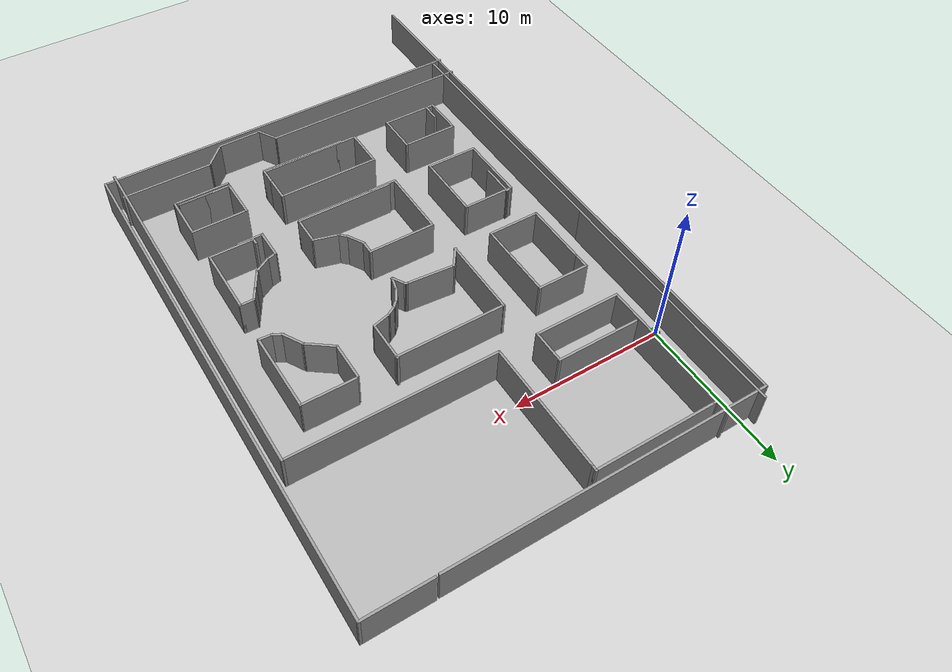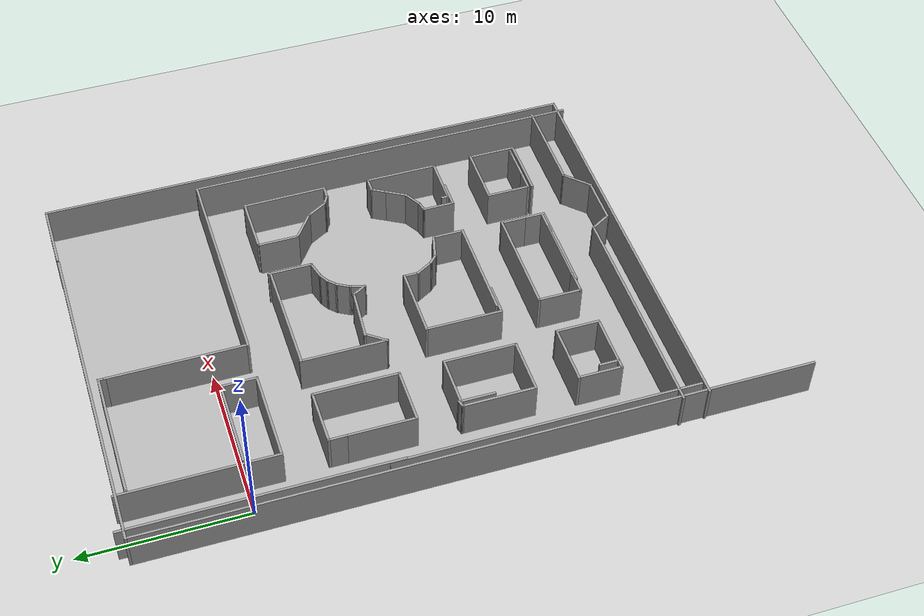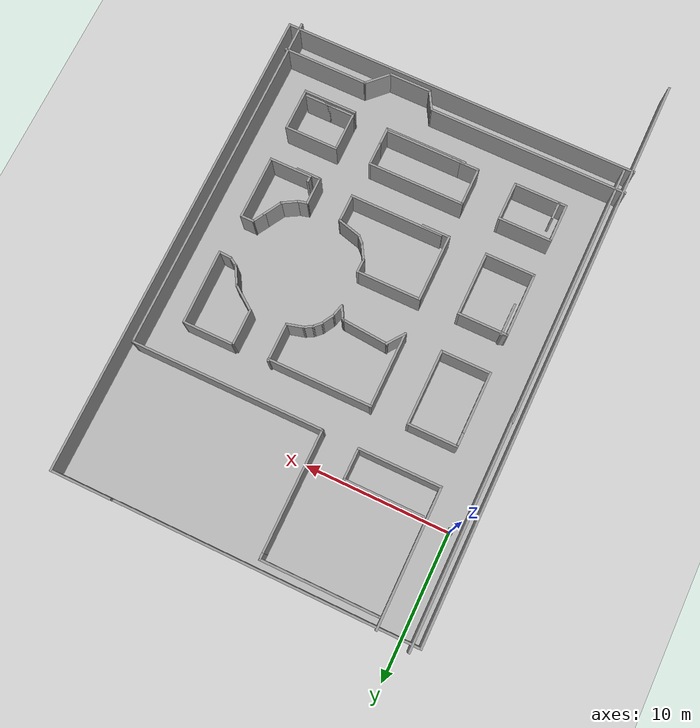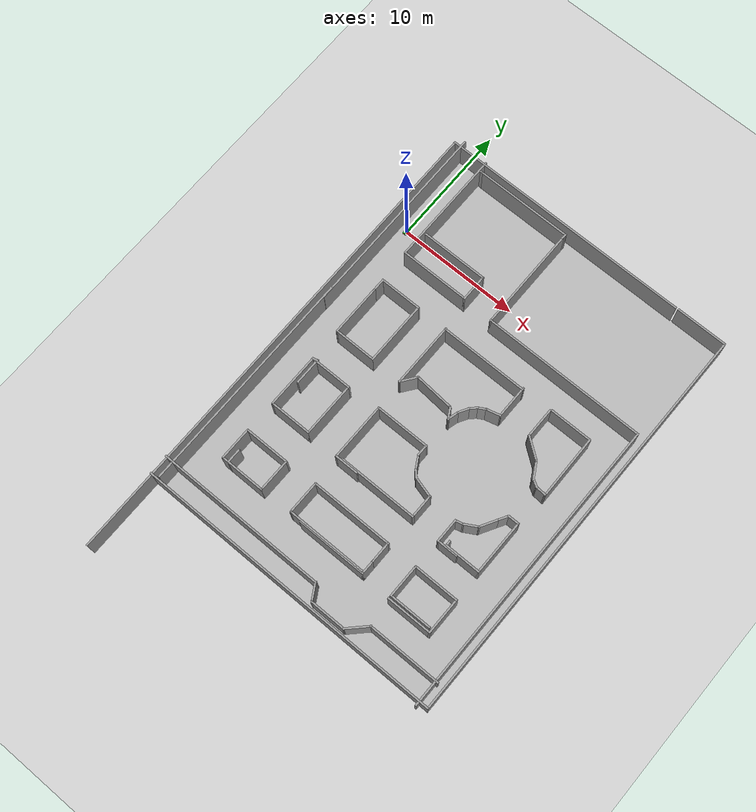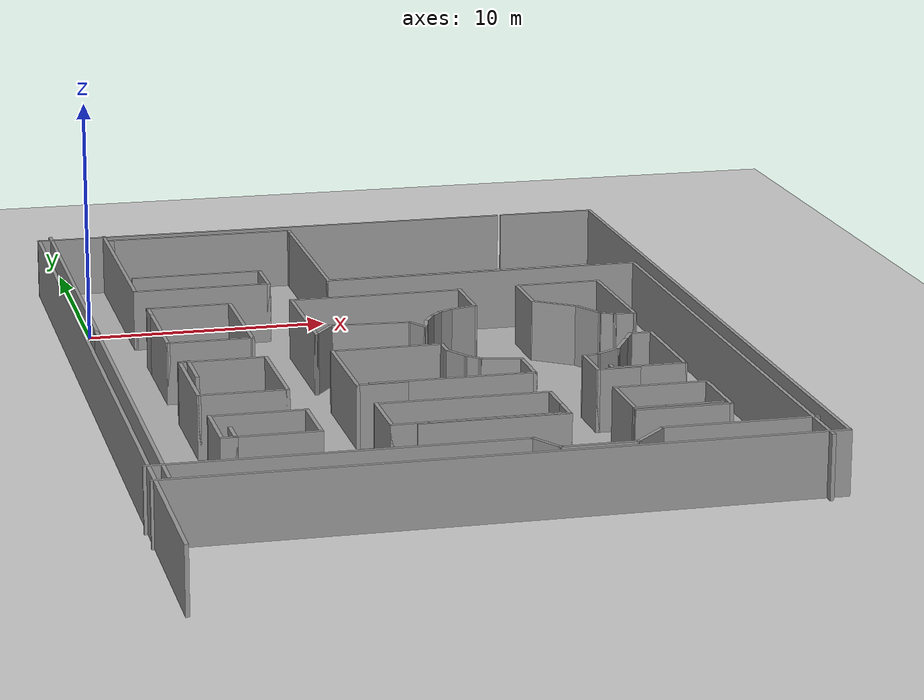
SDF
<sdf version="1.7">
 <world name="default">
  <light name="sun" type="directional">
   <pose>0 0 10 0 -0 0</pose>
   <diffuse>0.8 0.8 0.8 1</diffuse>
   <specular>0.2 0.2 0.2 1</specular>
   <attenuation>
    <range>1000</range>
    <constant>0.9</constant>
    <linear>0.01</linear>
    <quadratic>0.001</quadratic>
   </attenuation>
   <direction>-0.5 0.1 -0.9</direction>
   <spot><inner_angle>0</inner_angle><outer_angle>0</outer_angle><falloff>0</falloff></spot>
  </light>
  <model name="ground_plane">
   <static>1</static>
   <link name="link">
    <collision name="collision">
     <geometry><plane><normal>0 0 1</normal><size>100 100</size></plane></geometry>
     <surface>
      <contact><collide_bitmask>65535</collide_bitmask></contact>
      <friction><ode><mu>100</mu><mu2>50</mu2></ode></friction>
     </surface>
    </collision>
    <visual name="visual">
     <cast_shadows>0</cast_shadows>
     <geometry><plane><normal>0 0 1</normal><size>100 100</size></plane></geometry>
     <material>
      <script><uri>file://media/materials/scripts/gazebo.material</uri><name>Gazebo/Grey</name></script>
     </material>
    </visual>
   </link>
  </model>
  <gravity>0 0 -9.8</gravity>
  <magnetic_field>6e-06 2.3e-05 -4.2e-05</magnetic_field>
  <atmosphere type="adiabatic"/>
  <physics type="ode">
   <max_step_size>0.001</max_step_size>
   <real_time_factor>1</real_time_factor>
   <real_time_update_rate>1000</real_time_update_rate>
  </physics>
  <scene><ambient>0.4 0.4 0.4 1</ambient><background>0.7 0.7 0.7 1</background><shadows>1</shadows></scene>
  <spherical_coordinates>
   <surface_model>EARTH_WGS84</surface_model>
   <latitude_deg>0</latitude_deg>
   <longitude_deg>0</longitude_deg>
   <elevation>0</elevation>
   <heading_deg>0</heading_deg>
  </spherical_coordinates>
  <model name="/">
   <link name="base_footprint">
    <inertial>
     <pose>0.002427 0 0.002184 0 -0 0</pose>
     <mass>10.3</mass>
     <inertia>
      <ixx>0.110946</ixx>
      <ixy>0</ixy>
      <ixz>5.46117e-05</ixz>
      <iyy>0.25039</iyy>
      <iyz>0</iyz>
      <izz>0.289674</izz>
     </inertia>
    </inertial>
    <collision name="base_footprint_collision">
     <geometry><box><size>0.5 0.3 0.2</size></box></geometry>
    </collision>
    <collision name="base_footprint_fixed_joint_lump__camera_link_collision_1">
     <pose>0.25 0 0 0 -0 0</pose>
     <geometry><box><size>0.025 0.1 0.025</size></box></geometry>
    </collision>
    <collision name="base_footprint_fixed_joint_lump__laser_link_collision_2">
     <pose>0 0 0.1125 0 -0 0</pose>
     <geometry><cylinder><length>0.025</length><radius>0.025</radius></cylinder></geometry>
    </collision>
    <visual name="base_footprint_visual">
     <geometry><box><size>0.5 0.3 0.2</size></box></geometry>
     <material>
      <script><name>Gazebo/Green</name><uri>file://media/materials/scripts/gazebo.material</uri></script>
     </material>
    </visual>
    <visual name="base_footprint_fixed_joint_lump__camera_link_visual_1">
     <pose>0.25 0 0 0 -0 0</pose>
     <geometry><box><size>0.025 0.1 0.025</size></box></geometry>
     <material>
      <script><name>Gazebo/Red</name><uri>file://media/materials/scripts/gazebo.material</uri></script>
     </material>
    </visual>
    <visual name="base_footprint_fixed_joint_lump__laser_link_visual_2">
     <pose>0 0 0.1125 0 -0 0</pose>
     <geometry><cylinder><length>0.025</length><radius>0.025</radius></cylinder></geometry>
     <material>
      <script><name>Gazebo/Yellow</name><uri>file://media/materials/scripts/gazebo.material</uri></script>
     </material>
    </visual>
    <sensor name="camera_link_camera" type="depth">
     <update_rate>20</update_rate>
     <camera>
      <horizontal_fov>1.0472</horizontal_fov>
      <image><width>640</width><height>480</height><format>R8G8B8</format></image>
      <clip><near>0.05</near><far>3</far></clip>
     </camera>
     <plugin name="camera_link_controller" filename="libgazebo_ros_openni_kinect.so">
      <baseline>0.2</baseline>
      <alwaysOn>1</alwaysOn>
      <updateRate>1.0</updateRate>
      <imageTopicName>/camera/rgb/image_raw</imageTopicName>
      <cameraInfoTopicName>/camera/rgb/camera_info</cameraInfoTopicName>
      <depthImageTopicName>/camera/depth/image_raw</depthImageTopicName>
      <depthImageInfoTopicName>/camera/depth/camera_info</depthImageInfoTopicName>
      <pointCloudTopicName>/camera/depth/points</pointCloudTopicName>
      <frameName>camera_link</frameName>
      <pointCloudCutoff>0.5</pointCloudCutoff>
      <pointCloudCutoffMax>3.0</pointCloudCutoffMax>
      <distortionK1>0.00000001</distortionK1>
      <distortionK2>0.00000001</distortionK2>
      <distortionK3>0.00000001</distortionK3>
      <distortionT1>0.00000001</distortionT1>
      <distortionT2>0.00000001</distortionT2>
      <CxPrime>0</CxPrime>
      <Cx>0</Cx>
      <Cy>0</Cy>
      <focalLength>0</focalLength>
      <hackBaseline>0</hackBaseline>
      <robotNamespace>/</robotNamespace>
     </plugin>
     <pose>0.25 0 0 0 -0 0</pose>
    </sensor>
    <sensor name="head_hokuyo_sensor" type="gpu_ray">
     <visualize>0</visualize>
     <update_rate>40</update_rate>
     <ray>
      <scan>
       <horizontal>
        <samples>720</samples>
        <resolution>1</resolution>
        <min_angle>-3.1415</min_angle>
        <max_angle>3.1415</max_angle>
       </horizontal>
       <vertical><samples>1</samples><min_angle>0</min_angle><max_angle>0</max_angle></vertical>
      </scan>
      <range><min>0.1</min><max>10</max><resolution>0.01</resolution></range>
      <noise><type>gaussian</type><mean>0</mean><stddev>0.01</stddev></noise>
     </ray>
     <plugin name="gazebo_ros_head_hokuyo_controller" filename="libgazebo_ros_gpu_laser.so">
      <topicName>scan</topicName>
      <frameName>laser_link</frameName>
      <robotNamespace>/</robotNamespace>
     </plugin>
     <pose>0 0 0.1125 0 -0 0</pose>
    </sensor>
   </link>
   <joint name="caster_wheel_back_base" type="revolute">
    <pose relative_to="base_footprint">-0.2 0 -0.15 0 -0 0</pose>
    <parent>base_footprint</parent>
    <child>caster_wheel_back_link</child>
    <axis>
     <xyz>1 1 1</xyz>
     <limit><lower>-1e+16</lower><upper>1e+16</upper></limit>
     <dynamics><spring_reference>0</spring_reference><spring_stiffness>0</spring_stiffness></dynamics>
    </axis>
   </joint>
   <link name="caster_wheel_back_link">
    <pose relative_to="caster_wheel_back_base">0 0 0 0 -0 0</pose>
    <inertial>
     <mass>0.05</mass>
     <inertia><ixx>5e-05</ixx><ixy>0</ixy><ixz>0</ixz><iyy>5e-05</iyy><iyz>0</iyz><izz>5e-05</izz></inertia>
    </inertial>
    <collision name="caster_wheel_back_link_collision">
     <geometry><sphere><radius>0.05</radius></sphere></geometry>
    </collision>
    <visual name="caster_wheel_back_link_visual">
     <geometry><sphere><radius>0.05</radius></sphere></geometry>
     <material>
      <script><name>Gazebo/White</name><uri>file://media/materials/scripts/gazebo.material</uri></script>
     </material>
    </visual>
   </link>
   <joint name="caster_wheel_front_base" type="revolute">
    <pose relative_to="base_footprint">0.2 0 -0.15 0 -0 0</pose>
    <parent>base_footprint</parent>
    <child>caster_wheel_front_link</child>
    <axis>
     <xyz>1 1 1</xyz>
     <limit><lower>-1e+16</lower><upper>1e+16</upper></limit>
     <dynamics><spring_reference>0</spring_reference><spring_stiffness>0</spring_stiffness></dynamics>
    </axis>
   </joint>
   <link name="caster_wheel_front_link">
    <pose relative_to="caster_wheel_front_base">0 0 0 0 -0 0</pose>
    <inertial>
     <mass>0.05</mass>
     <inertia><ixx>5e-05</ixx><ixy>0</ixy><ixz>0</ixz><iyy>5e-05</iyy><iyz>0</iyz><izz>5e-05</izz></inertia>
    </inertial>
    <collision name="caster_wheel_front_link_collision">
     <geometry><sphere><radius>0.05</radius></sphere></geometry>
    </collision>
    <visual name="caster_wheel_front_link_visual">
     <geometry><sphere><radius>0.05</radius></sphere></geometry>
     <material>
      <script><name>Gazebo/White</name><uri>file://media/materials/scripts/gazebo.material</uri></script>
     </material>
    </visual>
   </link>
   <joint name="wheel_left_base" type="revolute">
    <pose relative_to="base_footprint">0 -0.175 -0.1 0 -0 0</pose>
    <parent>base_footprint</parent>
    <child>wheel_left_link</child>
    <axis>
     <xyz>0 1 0</xyz>
     <limit><lower>-1e+16</lower><upper>1e+16</upper></limit>
     <dynamics><spring_reference>0</spring_reference><spring_stiffness>0</spring_stiffness></dynamics>
    </axis>
   </joint>
   <link name="wheel_left_link">
    <pose relative_to="wheel_left_base">0 0 0 0 -0 0</pose>
    <inertial>
     <mass>0.5</mass>
     <inertia>
      <ixx>0.00135417</ixx>
      <ixy>0</ixy>
      <ixz>0</ixz>
      <iyy>0.00135417</iyy>
      <iyz>0</iyz>
      <izz>0.0025</izz>
     </inertia>
    </inertial>
    <collision name="wheel_left_link_collision">
     <pose>0 0 0 1.57079 1.57079 3.14159</pose>
     <geometry><cylinder><length>0.05</length><radius>0.1</radius></cylinder></geometry>
    </collision>
    <visual name="wheel_left_link_visual">
     <pose>0 0 0 1.57079 1.57079 3.14159</pose>
     <geometry><cylinder><length>0.05</length><radius>0.1</radius></cylinder></geometry>
     <material>
      <script><name>Gazebo/Black</name><uri>file://media/materials/scripts/gazebo.material</uri></script>
     </material>
    </visual>
   </link>
   <joint name="wheel_right_base" type="revolute">
    <pose relative_to="base_footprint">0 0.175 -0.1 0 -0 0</pose>
    <parent>base_footprint</parent>
    <child>wheel_right_link</child>
    <axis>
     <xyz>0 1 0</xyz>
     <limit><lower>-1e+16</lower><upper>1e+16</upper></limit>
     <dynamics><spring_reference>0</spring_reference><spring_stiffness>0</spring_stiffness></dynamics>
    </axis>
   </joint>
   <link name="wheel_right_link">
    <pose relative_to="wheel_right_base">0 0 0 0 -0 0</pose>
    <inertial>
     <mass>0.5</mass>
     <inertia>
      <ixx>0.00135417</ixx>
      <ixy>0</ixy>
      <ixz>0</ixz>
      <iyy>0.00135417</iyy>
      <iyz>0</iyz>
      <izz>0.0025</izz>
     </inertia>
    </inertial>
    <collision name="wheel_right_link_collision">
     <pose>0 0 0 1.57079 1.57079 3.14159</pose>
     <geometry><cylinder><length>0.05</length><radius>0.1</radius></cylinder></geometry>
    </collision>
    <visual name="wheel_right_link_visual">
     <pose>0 0 0 1.57079 1.57079 3.14159</pose>
     <geometry><cylinder><length>0.05</length><radius>0.1</radius></cylinder></geometry>
     <material>
      <script><name>Gazebo/Black</name><uri>file://media/materials/scripts/gazebo.material</uri></script>
     </material>
    </visual>
   </link>
   <static>0</static>
   <plugin name="differential_drive_controller" filename="libgazebo_ros_diff_drive.so">
    <updateRate>10.0</updateRate>
    <leftJoint>wheel_left_base</leftJoint>
    <rightJoint>wheel_right_base</rightJoint>
    <wheelSeparation>0.35</wheelSeparation>
    <wheelDiameter>0.2</wheelDiameter>
    <wheelAcceleration>0.0</wheelAcceleration>
    <wheelTorque>5</wheelTorque>
    <commandTopic>cmd_vel</commandTopic>
    <odometryTopic>odom</odometryTopic>
    <odometryFrame>odom</odometryFrame>
    <robotBaseFrame>base_footprint</robotBaseFrame>
    <odometrySource>1</odometrySource>
    <publishWheelTF>0</publishWheelTF>
    <publishOdom>1</publishOdom>
    <publishWheelJointState>0</publishWheelJointState>
    <legacyMode>1</legacyMode>
    <robotNamespace>/</robotNamespace>
   </plugin>
   <pose>-0.003729 -0.045002 0.2 -0 1.1e-05 -1.5475</pose>
  </model>
  <model name="zemin3">
   <link name="link">
    <inertial>
     <mass>1</mass>
     <inertia>
      <ixx>0.166667</ixx>
      <ixy>0</ixy>
      <ixz>0</ixz>
      <iyy>0.166667</iyy>
      <iyz>0</iyz>
      <izz>0.166667</izz>
     </inertia>
    </inertial>
    <visual name="visual">
     <geometry><box><size>25.1 33.33 0.002784</size></box></geometry>
     <material>
      <script>
       <uri>model://zemin2/materials/scripts/repeated.material</uri>
       <uri>model://zemin2/materials/textures/parkurrr.png</uri>
       <name>RepeatedTexture21</name>
      </script>
      <shader type="pixel"><normal_map>__default__</normal_map></shader>
      <ambient>0.18 0.204 0.212 1</ambient>
      <diffuse>0.7 0.7 0.7 1</diffuse>
      <specular>0.01 0.01 0.01 1</specular>
      <emissive>0 0 0 1</emissive>
     </material>
    </visual>
    <collision name="collision">
     <geometry><box><size>1 1 0.002784</size></box></geometry>
     <surface>
      <friction>
       <ode><mu>1</mu><mu2>1</mu2><fdir1>0 0 0</fdir1><slip1>0</slip1><slip2>0</slip2></ode>
       <torsional>
        <coefficient>1</coefficient>
        <patch_radius>0</patch_radius>
        <surface_radius>0</surface_radius>
        <use_patch_radius>1</use_patch_radius>
        <ode><slip>0</slip></ode>
       </torsional>
      </friction>
      <bounce><restitution_coefficient>0</restitution_coefficient><threshold>1e+06</threshold></bounce>
      <contact>
       <collide_without_contact>0</collide_without_contact>
       <collide_without_contact_bitmask>1</collide_without_contact_bitmask>
       <collide_bitmask>1</collide_bitmask>
       <ode>
        <soft_cfm>0</soft_cfm>
        <soft_erp>0.2</soft_erp>
        <kp>1e+13</kp>
        <kd>1</kd>
        <max_vel>0.01</max_vel>
        <min_depth>0</min_depth>
       </ode>
       <bullet>
        <split_impulse>1</split_impulse>
        <split_impulse_penetration_threshold>-0.01</split_impulse_penetration_threshold>
        <soft_cfm>0</soft_cfm>
        <soft_erp>0.2</soft_erp>
        <kp>1e+13</kp>
        <kd>1</kd>
       </bullet>
      </contact>
     </surface>
    </collision>
   </link>
   <static>1</static>
   <pose>11.274 -9.54487 0 0 -0 0</pose>
  </model>
  <model name="bariyers">
   <pose>11.2343 -12.5842 0 0 -0 0</pose>
   <link name="Wall_10">
    <collision name="Wall_10_Collision">
     <geometry><box><size>33.5 0.15 2.5</size></box></geometry>
     <pose>0 0 1.25 0 -0 0</pose>
    </collision>
    <visual name="Wall_10_Visual">
     <pose>0 0 1.25 0 -0 0</pose>
     <geometry><box><size>33.5 0.15 2.5</size></box></geometry>
     <material>
      <script><uri>file://media/materials/scripts/gazebo.material</uri><name>Gazebo/Grey</name></script>
      <ambient>1 1 1 1</ambient>
     </material>
     <meta><layer>0</layer></meta>
    </visual>
    <pose>12.5575 3.03271 0 0 -0 1.5708</pose>
   </link>
   <link name="Wall_100">
    <collision name="Wall_100_Collision">
     <geometry><box><size>1.75 0.15 2.5</size></box></geometry>
     <pose>0 0 1.25 0 -0 0</pose>
    </collision>
    <visual name="Wall_100_Visual">
     <pose>0 0 1.25 0 -0 0</pose>
     <geometry><box><size>1.75 0.15 2.5</size></box></geometry>
     <material>
      <script><uri>file://media/materials/scripts/gazebo.material</uri><name>Gazebo/Grey</name></script>
      <ambient>1 1 1 1</ambient>
     </material>
     <meta><layer>0</layer></meta>
    </visual>
    <pose>2.68549 -2.25618 0 0 -0 2.87979</pose>
   </link>
   <link name="Wall_101">
    <collision name="Wall_101_Collision">
     <geometry><box><size>0.75 0.15 2.5</size></box></geometry>
     <pose>0 0 1.25 0 -0 0</pose>
    </collision>
    <visual name="Wall_101_Visual">
     <pose>0 0 1.25 0 -0 0</pose>
     <geometry><box><size>0.75 0.15 2.5</size></box></geometry>
     <material>
      <script><uri>file://media/materials/scripts/gazebo.material</uri><name>Gazebo/Grey</name></script>
      <ambient>1 1 1 1</ambient>
     </material>
     <meta><layer>0</layer></meta>
    </visual>
    <pose>1.70062 -1.83699 0 0 -0 2.35619</pose>
   </link>
   <link name="Wall_102">
    <collision name="Wall_102_Collision">
     <geometry><box><size>1.25 0.15 2.5</size></box></geometry>
     <pose>0 0 1.25 0 -0 0</pose>
    </collision>
    <visual name="Wall_102_Visual">
     <pose>0 0 1.25 0 -0 0</pose>
     <geometry><box><size>1.25 0.15 2.5</size></box></geometry>
     <material>
      <script><uri>file://media/materials/scripts/gazebo.material</uri><name>Gazebo/Grey</name></script>
      <ambient>1 1 1 1</ambient>
     </material>
     <meta><layer>0</layer></meta>
    </visual>
    <pose>1.21349 -1.14855 0 0 -0 2.0944</pose>
   </link>
   <link name="Wall_103">
    <collision name="Wall_103_Collision">
     <geometry><box><size>1 0.15 2.5</size></box></geometry>
     <pose>0 0 1.25 0 -0 0</pose>
    </collision>
    <visual name="Wall_103_Visual">
     <pose>0 0 1.25 0 -0 0</pose>
     <geometry><box><size>1 0.15 2.5</size></box></geometry>
     <material>
      <script><uri>file://media/materials/scripts/gazebo.material</uri><name>Gazebo/Grey</name></script>
      <ambient>1 1 1 1</ambient>
     </material>
     <meta><layer>0</layer></meta>
    </visual>
    <pose>0.938488 -0.247233 0 0 -0 1.5708</pose>
   </link>
   <link name="Wall_104">
    <collision name="Wall_104_Collision">
     <geometry><box><size>4.5 0.15 2.5</size></box></geometry>
     <pose>0 0 1.25 0 -0 0</pose>
    </collision>
    <visual name="Wall_104_Visual">
     <pose>0 0 1.25 0 -0 0</pose>
     <geometry><box><size>4.5 0.15 2.5</size></box></geometry>
     <material>
      <script><uri>file://media/materials/scripts/gazebo.material</uri><name>Gazebo/Grey</name></script>
      <ambient>1 1 1 1</ambient>
     </material>
     <meta><layer>0</layer></meta>
    </visual>
    <pose>-1.23651 0.177767 0 0 -0 3.14159</pose>
   </link>
   <link name="Wall_105">
    <collision name="Wall_105_Collision">
     <geometry><box><size>4.75 0.15 2.5</size></box></geometry>
     <pose>0 0 1.25 0 -0 0</pose>
    </collision>
    <visual name="Wall_105_Visual">
     <pose>0 0 1.25 0 -0 0</pose>
     <geometry><box><size>4.75 0.15 2.5</size></box></geometry>
     <material>
      <script><uri>file://media/materials/scripts/gazebo.material</uri><name>Gazebo/Grey</name></script>
      <ambient>1 1 1 1</ambient>
     </material>
     <meta><layer>0</layer></meta>
    </visual>
    <pose>-3.41151 -2.12223 0 0 -0 -1.5708</pose>
   </link>
   <link name="Wall_106">
    <collision name="Wall_106_Collision">
     <geometry><box><size>2 0.15 2.5</size></box></geometry>
     <pose>0 0 1.25 0 -0 0</pose>
    </collision>
    <visual name="Wall_106_Visual">
     <pose>0 0 1.25 0 -0 0</pose>
     <geometry><box><size>2 0.15 2.5</size></box></geometry>
     <material>
      <script><uri>file://media/materials/scripts/gazebo.material</uri><name>Gazebo/Grey</name></script>
      <ambient>1 1 1 1</ambient>
     </material>
     <meta><layer>0</layer></meta>
    </visual>
    <pose>-2.48651 -4.42223 0 0 -0 0</pose>
   </link>
   <link name="Wall_109">
    <collision name="Wall_109_Collision">
     <geometry><box><size>8.5 0.15 2.5</size></box></geometry>
     <pose>0 0 1.25 0 -0 0</pose>
    </collision>
    <visual name="Wall_109_Visual">
     <pose>0 0 1.25 0 -0 0</pose>
     <geometry><box><size>8.5 0.15 2.5</size></box></geometry>
     <material>
      <script><uri>file://media/materials/scripts/gazebo.material</uri><name>Gazebo/Grey</name></script>
      <ambient>1 1 1 1</ambient>
     </material>
     <meta><layer>0</layer></meta>
    </visual>
    <pose>-1.45811 14.5463 0 0 -0 -1.5708</pose>
   </link>
   <link name="Wall_11">
    <collision name="Wall_11_Collision">
     <geometry><box><size>4.25 0.15 2.5</size></box></geometry>
     <pose>0 0 1.25 0 -0 0</pose>
    </collision>
    <visual name="Wall_11_Visual">
     <pose>0 0 1.25 0 -0 0</pose>
     <geometry><box><size>4.25 0.15 2.5</size></box></geometry>
     <material>
      <script><uri>file://media/materials/scripts/gazebo.material</uri><name>Gazebo/Grey</name></script>
      <ambient>1 1 1 1</ambient>
     </material>
     <meta><layer>0</layer></meta>
    </visual>
    <pose>10.5075 19.7077 0 0 -0 3.14159</pose>
   </link>
   <link name="Wall_110">
    <collision name="Wall_110_Collision">
     <geometry><box><size>13.4314 0.15 2.5</size></box></geometry>
     <pose>0 0 1.25 0 -0 0</pose>
    </collision>
    <visual name="Wall_110_Visual">
     <pose>0 0 1.25 0 -0 0</pose>
     <geometry><box><size>13.4314 0.15 2.5</size></box></geometry>
     <material>
      <script><uri>file://media/materials/scripts/gazebo.material</uri><name>Gazebo/Grey</name></script>
      <ambient>1 1 1 1</ambient>
     </material>
     <meta><layer>0</layer></meta>
    </visual>
    <pose>5.18256 10.3713 0 0 -0 0</pose>
   </link>
   <link name="Wall_111">
    <collision name="Wall_111_Collision">
     <geometry><box><size>24.5 0.15 2.5</size></box></geometry>
     <pose>0 0 1.25 0 -0 0</pose>
    </collision>
    <visual name="Wall_111_Visual">
     <pose>0 0 1.25 0 -0 0</pose>
     <geometry><box><size>24.5 0.15 2.5</size></box></geometry>
     <material>
      <script><uri>file://media/materials/scripts/gazebo.material</uri><name>Gazebo/Grey</name></script>
      <ambient>1 1 1 1</ambient>
     </material>
     <meta><layer>0</layer></meta>
    </visual>
    <pose>11.8232 -1.80369 0 0 -0 -1.5708</pose>
   </link>
   <link name="Wall_115">
    <collision name="Wall_115_Collision">
     <geometry><box><size>1.25 0.15 2.5</size></box></geometry>
     <pose>0 0 1.25 0 -0 0</pose>
    </collision>
    <visual name="Wall_115_Visual">
     <pose>0 0 1.25 0 -0 0</pose>
     <geometry><box><size>1.25 0.15 2.5</size></box></geometry>
     <material>
      <script><uri>file://media/materials/scripts/gazebo.material</uri><name>Gazebo/Grey</name></script>
      <ambient>1 1 1 1</ambient>
     </material>
     <meta><layer>0</layer></meta>
    </visual>
    <pose>3.00193 5.10047 0 0 -0 -2.87979</pose>
   </link>
   <link name="Wall_116">
    <collision name="Wall_116_Collision">
     <geometry><box><size>0.75 0.15 2.5</size></box></geometry>
     <pose>0 0 1.25 0 -0 0</pose>
    </collision>
    <visual name="Wall_116_Visual">
     <pose>0 0 1.25 0 -0 0</pose>
     <geometry><box><size>0.75 0.15 2.5</size></box></geometry>
     <material>
      <script><uri>file://media/materials/scripts/gazebo.material</uri><name>Gazebo/Grey</name></script>
      <ambient>1 1 1 1</ambient>
     </material>
     <meta><layer>0</layer></meta>
    </visual>
    <pose>2.21086 4.80812 0 0 -0 -2.61799</pose>
   </link>
   <link name="Wall_117">
    <collision name="Wall_117_Collision">
     <geometry><box><size>0.75 0.15 2.5</size></box></geometry>
     <pose>0 0 1.25 0 -0 0</pose>
    </collision>
    <visual name="Wall_117_Visual">
     <pose>0 0 1.25 0 -0 0</pose>
     <geometry><box><size>0.75 0.15 2.5</size></box></geometry>
     <material>
      <script><uri>file://media/materials/scripts/gazebo.material</uri><name>Gazebo/Grey</name></script>
      <ambient>1 1 1 1</ambient>
     </material>
     <meta><layer>0</layer></meta>
    </visual>
    <pose>1.73892 4.44599 0 0 -0 -2.35619</pose>
   </link>
   <link name="Wall_118">
    <collision name="Wall_118_Collision">
     <geometry><box><size>1 0.15 2.5</size></box></geometry>
     <pose>0 0 1.25 0 -0 0</pose>
    </collision>
    <visual name="Wall_118_Visual">
     <pose>0 0 1.25 0 -0 0</pose>
     <geometry><box><size>1 0.15 2.5</size></box></geometry>
     <material>
      <script><uri>file://media/materials/scripts/gazebo.material</uri><name>Gazebo/Grey</name></script>
      <ambient>1 1 1 1</ambient>
     </material>
     <meta><layer>0</layer></meta>
    </visual>
    <pose>1.31429 3.8658 0 0 -0 -2.0944</pose>
   </link>
   <link name="Wall_119">
    <collision name="Wall_119_Collision">
     <geometry><box><size>1 0.15 2.5</size></box></geometry>
     <pose>0 0 1.25 0 -0 0</pose>
    </collision>
    <visual name="Wall_119_Visual">
     <pose>0 0 1.25 0 -0 0</pose>
     <geometry><box><size>1 0.15 2.5</size></box></geometry>
     <material>
      <script><uri>file://media/materials/scripts/gazebo.material</uri><name>Gazebo/Grey</name></script>
      <ambient>1 1 1 1</ambient>
     </material>
     <meta><layer>0</layer></meta>
    </visual>
    <pose>0.991789 3.08722 0 0 -0 -1.8326</pose>
   </link>
   <link name="Wall_120">
    <collision name="Wall_120_Collision">
     <geometry><box><size>1 0.15 2.5</size></box></geometry>
     <pose>0 0 1.25 0 -0 0</pose>
    </collision>
    <visual name="Wall_120_Visual">
     <pose>0 0 1.25 0 -0 0</pose>
     <geometry><box><size>1 0.15 2.5</size></box></geometry>
     <material>
      <script><uri>file://media/materials/scripts/gazebo.material</uri><name>Gazebo/Grey</name></script>
      <ambient>1 1 1 1</ambient>
     </material>
     <meta><layer>0</layer></meta>
    </visual>
    <pose>0.669291 3.04476 0 0 -0 2.0944</pose>
   </link>
   <link name="Wall_121">
    <collision name="Wall_121_Collision">
     <geometry><box><size>0.25 0.15 2.5</size></box></geometry>
     <pose>0 0 1.25 0 -0 0</pose>
    </collision>
    <visual name="Wall_121_Visual">
     <pose>0 0 1.25 0 -0 0</pose>
     <geometry><box><size>0.25 0.15 2.5</size></box></geometry>
     <material>
      <script><uri>file://media/materials/scripts/gazebo.material</uri><name>Gazebo/Grey</name></script>
      <ambient>1 1 1 1</ambient>
     </material>
     <meta><layer>0</layer></meta>
    </visual>
    <pose>0.41349 3.43782 0 0 -0 2.61799</pose>
   </link>
   <link name="Wall_122">
    <collision name="Wall_122_Collision">
     <geometry><box><size>3.29431 0.15 2.5</size></box></geometry>
     <pose>0 0 1.25 0 -0 0</pose>
    </collision>
    <visual name="Wall_122_Visual">
     <pose>0 0 1.25 0 -0 0</pose>
     <geometry><box><size>3.29431 0.15 2.5</size></box></geometry>
     <material>
      <script><uri>file://media/materials/scripts/gazebo.material</uri><name>Gazebo/Grey</name></script>
      <ambient>1 1 1 1</ambient>
     </material>
     <meta><layer>0</layer></meta>
    </visual>
    <pose>-1.19703 3.58726 0 0 -0 3.06235</pose>
   </link>
   <link name="Wall_123">
    <collision name="Wall_123_Collision">
     <geometry><box><size>1.5149 0.15 2.5</size></box></geometry>
     <pose>0 0 1.25 0 -0 0</pose>
    </collision>
    <visual name="Wall_123_Visual">
     <pose>0 0 1.25 0 -0 0</pose>
     <geometry><box><size>1.5149 0.15 2.5</size></box></geometry>
     <material>
      <script><uri>file://media/materials/scripts/gazebo.material</uri><name>Gazebo/Grey</name></script>
      <ambient>1 1 1 1</ambient>
     </material>
     <meta><layer>0</layer></meta>
    </visual>
    <pose>-3.13489 3.1633 0 0 -0 -2.2083</pose>
   </link>
   <link name="Wall_128">
    <collision name="Wall_128_Collision">
     <geometry><box><size>2.75 0.15 2.5</size></box></geometry>
     <pose>0 0 1.25 0 -0 0</pose>
    </collision>
    <visual name="Wall_128_Visual">
     <pose>0 0 1.25 0 -0 0</pose>
     <geometry><box><size>2.75 0.15 2.5</size></box></geometry>
     <material>
      <script><uri>file://media/materials/scripts/gazebo.material</uri><name>Gazebo/Grey</name></script>
      <ambient>1 1 1 1</ambient>
     </material>
     <meta><layer>0</layer></meta>
    </visual>
    <pose>3.53319 6.54282 0 0 -0 1.5708</pose>
   </link>
   <link name="Wall_131">
    <collision name="Wall_131_Collision">
     <geometry><box><size>5.32111 0.15 2.5</size></box></geometry>
     <pose>0 0 1.25 0 -0 0</pose>
    </collision>
    <visual name="Wall_131_Visual">
     <pose>0 0 1.25 0 -0 0</pose>
     <geometry><box><size>5.32111 0.15 2.5</size></box></geometry>
     <material>
      <script><uri>file://media/materials/scripts/gazebo.material</uri><name>Gazebo/Grey</name></script>
      <ambient>1 1 1 1</ambient>
     </material>
     <meta><layer>0</layer></meta>
    </visual>
    <pose>-3.54107 5.20045 0 0 -0 1.5708</pose>
   </link>
   <link name="Wall_132">
    <collision name="Wall_132_Collision">
     <geometry><box><size>7.25 0.15 2.5</size></box></geometry>
     <pose>0 0 1.25 0 -0 0</pose>
    </collision>
    <visual name="Wall_132_Visual">
     <pose>0 0 1.25 0 -0 0</pose>
     <geometry><box><size>7.25 0.15 2.5</size></box></geometry>
     <material>
      <script><uri>file://media/materials/scripts/gazebo.material</uri><name>Gazebo/Grey</name></script>
      <ambient>1 1 1 1</ambient>
     </material>
     <meta><layer>0</layer></meta>
    </visual>
    <pose>0.008928 7.75045 0 0 -0 0</pose>
   </link>
   <link name="Wall_135">
    <collision name="Wall_135_Collision">
     <geometry><box><size>2.5 0.15 2.5</size></box></geometry>
     <pose>0 0 1.25 0 -0 0</pose>
    </collision>
    <visual name="Wall_135_Visual">
     <pose>0 0 1.25 0 -0 0</pose>
     <geometry><box><size>2.5 0.15 2.5</size></box></geometry>
     <material>
      <script><uri>file://media/materials/scripts/gazebo.material</uri><name>Gazebo/Grey</name></script>
      <ambient>1 1 1 1</ambient>
     </material>
     <meta><layer>0</layer></meta>
    </visual>
    <pose>6.01396 6.59675 0 0 -0 -1.5708</pose>
   </link>
   <link name="Wall_136">
    <collision name="Wall_136_Collision">
     <geometry><box><size>2.008 0.15 2.5</size></box></geometry>
     <pose>0 0 1.25 0 -0 0</pose>
    </collision>
    <visual name="Wall_136_Visual">
     <pose>0 0 1.25 0 -0 0</pose>
     <geometry><box><size>2.008 0.15 2.5</size></box></geometry>
     <material>
      <script><uri>file://media/materials/scripts/gazebo.material</uri><name>Gazebo/Grey</name></script>
      <ambient>1 1 1 1</ambient>
     </material>
     <meta><layer>0</layer></meta>
    </visual>
    <pose>6.79735 4.83551 0 0 -0 -0.634766</pose>
   </link>
   <link name="Wall_137">
    <collision name="Wall_137_Collision">
     <geometry><box><size>1.5 0.15 2.5</size></box></geometry>
     <pose>0 0 1.25 0 -0 0</pose>
    </collision>
    <visual name="Wall_137_Visual">
     <pose>0 0 1.25 0 -0 0</pose>
     <geometry><box><size>1.5 0.15 2.5</size></box></geometry>
     <material>
      <script><uri>file://media/materials/scripts/gazebo.material</uri><name>Gazebo/Grey</name></script>
      <ambient>1 1 1 1</ambient>
     </material>
     <meta><layer>0</layer></meta>
    </visual>
    <pose>7.8829 3.70006 0 0 -0 -1.0472</pose>
   </link>
   <link name="Wall_138">
    <collision name="Wall_138_Collision">
     <geometry><box><size>0.75 0.15 2.5</size></box></geometry>
     <pose>0 0 1.25 0 -0 0</pose>
    </collision>
    <visual name="Wall_138_Visual">
     <pose>0 0 1.25 0 -0 0</pose>
     <geometry><box><size>0.75 0.15 2.5</size></box></geometry>
     <material>
      <script><uri>file://media/materials/scripts/gazebo.material</uri><name>Gazebo/Grey</name></script>
      <ambient>1 1 1 1</ambient>
     </material>
     <meta><layer>0</layer></meta>
    </visual>
    <pose>8.4802 2.96549 0 0 -0 -0.523599</pose>
   </link>
   <link name="Wall_139">
    <collision name="Wall_139_Collision">
     <geometry><box><size>0.912152 0.15 2.5</size></box></geometry>
     <pose>0 0 1.25 0 -0 0</pose>
    </collision>
    <visual name="Wall_139_Visual">
     <pose>0 0 1.25 0 -0 0</pose>
     <geometry><box><size>0.912152 0.15 2.5</size></box></geometry>
     <material>
      <script><uri>file://media/materials/scripts/gazebo.material</uri><name>Gazebo/Grey</name></script>
      <ambient>1 1 1 1</ambient>
     </material>
     <meta><layer>0</layer></meta>
    </visual>
    <pose>9.12036 2.79188 0 0 -0 -0.061994</pose>
   </link>
   <link name="Wall_140">
    <collision name="Wall_140_Collision">
     <geometry><box><size>5.25 0.15 2.5</size></box></geometry>
     <pose>0 0 1.25 0 -0 0</pose>
    </collision>
    <visual name="Wall_140_Visual">
     <pose>0 0 1.25 0 -0 0</pose>
     <geometry><box><size>5.25 0.15 2.5</size></box></geometry>
     <material>
      <script><uri>file://media/materials/scripts/gazebo.material</uri><name>Gazebo/Grey</name></script>
      <ambient>1 1 1 1</ambient>
     </material>
     <meta><layer>0</layer></meta>
    </visual>
    <pose>9.51838 5.31827 0 0 -0 1.57981</pose>
   </link>
   <link name="Wall_143">
    <collision name="Wall_143_Collision">
     <geometry><box><size>3.5 0.15 2.5</size></box></geometry>
     <pose>0 0 1.25 0 -0 0</pose>
    </collision>
    <visual name="Wall_143_Visual">
     <pose>0 0 1.25 0 -0 0</pose>
     <geometry><box><size>3.5 0.15 2.5</size></box></geometry>
     <material>
      <script><uri>file://media/materials/scripts/gazebo.material</uri><name>Gazebo/Grey</name></script>
      <ambient>1 1 1 1</ambient>
     </material>
     <meta><layer>0</layer></meta>
    </visual>
    <pose>7.8204 7.86827 0 0 -0 3.14159</pose>
   </link>
   <link name="Wall_145">
    <collision name="Wall_145_Collision">
     <geometry><box><size>6 0.15 2.5</size></box></geometry>
     <pose>0 0 1.25 0 -0 0</pose>
    </collision>
    <visual name="Wall_145_Visual">
     <pose>0 0 1.25 0 -0 0</pose>
     <geometry><box><size>6 0.15 2.5</size></box></geometry>
     <material>
      <script><uri>file://media/materials/scripts/gazebo.material</uri><name>Gazebo/Grey</name></script>
      <ambient>1 1 1 1</ambient>
     </material>
     <meta><layer>0</layer></meta>
    </visual>
    <pose>9.05069 -11.9195 0 0 -0 3.14159</pose>
   </link>
   <link name="Wall_146">
    <collision name="Wall_146_Collision">
     <geometry><box><size>2 0.15 2.5</size></box></geometry>
     <pose>0 0 1.25 0 -0 0</pose>
    </collision>
    <visual name="Wall_146_Visual">
     <pose>0 0 1.25 0 -0 0</pose>
     <geometry><box><size>2 0.15 2.5</size></box></geometry>
     <material>
      <script><uri>file://media/materials/scripts/gazebo.material</uri><name>Gazebo/Grey</name></script>
      <ambient>1 1 1 1</ambient>
     </material>
     <meta><layer>0</layer></meta>
    </visual>
    <pose>5.47162 -12.5735 0 0 -0 -2.35619</pose>
   </link>
   <link name="Wall_147">
    <collision name="Wall_147_Collision">
     <geometry><box><size>3 0.15 2.5</size></box></geometry>
     <pose>0 0 1.25 0 -0 0</pose>
    </collision>
    <visual name="Wall_147_Visual">
     <pose>0 0 1.25 0 -0 0</pose>
     <geometry><box><size>3 0.15 2.5</size></box></geometry>
     <material>
      <script><uri>file://media/materials/scripts/gazebo.material</uri><name>Gazebo/Grey</name></script>
      <ambient>1 1 1 1</ambient>
     </material>
     <meta><layer>0</layer></meta>
    </visual>
    <pose>3.39254 -13.2276 0 0 -0 3.14159</pose>
   </link>
   <link name="Wall_148">
    <collision name="Wall_148_Collision">
     <geometry><box><size>1.5 0.15 2.5</size></box></geometry>
     <pose>0 0 1.25 0 -0 0</pose>
    </collision>
    <visual name="Wall_148_Visual">
     <pose>0 0 1.25 0 -0 0</pose>
     <geometry><box><size>1.5 0.15 2.5</size></box></geometry>
     <material>
      <script><uri>file://media/materials/scripts/gazebo.material</uri><name>Gazebo/Grey</name></script>
      <ambient>1 1 1 1</ambient>
     </material>
     <meta><layer>0</layer></meta>
    </visual>
    <pose>1.63004 -12.643 0 0 -0 2.0944</pose>
   </link>
   <link name="Wall_149">
    <collision name="Wall_149_Collision">
     <geometry><box><size>14 0.15 2.5</size></box></geometry>
     <pose>0 0 1.25 0 -0 0</pose>
    </collision>
    <visual name="Wall_149_Visual">
     <pose>0 0 1.25 0 -0 0</pose>
     <geometry><box><size>14 0.15 2.5</size></box></geometry>
     <material>
      <script><uri>file://media/materials/scripts/gazebo.material</uri><name>Gazebo/Grey</name></script>
      <ambient>1 1 1 1</ambient>
     </material>
     <meta><layer>0</layer></meta>
    </visual>
    <pose>-5.63246 -12.0585 0 0 -0 3.14159</pose>
   </link>
   <link name="Wall_151">
    <collision name="Wall_151_Collision">
     <geometry><box><size>16.25 0.15 2.5</size></box></geometry>
     <pose>0 0 1.25 0 -0 0</pose>
    </collision>
    <visual name="Wall_151_Visual">
     <pose>0 0 1.25 0 -0 0</pose>
     <geometry><box><size>16.25 0.15 2.5</size></box></geometry>
     <material>
      <script><uri>file://media/materials/scripts/gazebo.material</uri><name>Gazebo/Grey</name></script>
      <ambient>1 1 1 1</ambient>
     </material>
     <meta><layer>0</layer></meta>
    </visual>
    <pose>-11.8908 12.1142 0 0 -0 -1.5708</pose>
   </link>
   <link name="Wall_153">
    <collision name="Wall_153_Collision">
     <geometry><box><size>18.5 0.15 2.5</size></box></geometry>
     <pose>0 0 1.25 0 -0 0</pose>
    </collision>
    <visual name="Wall_153_Visual">
     <pose>0 0 1.25 0 -0 0</pose>
     <geometry><box><size>18.5 0.15 2.5</size></box></geometry>
     <material>
      <script><uri>file://media/materials/scripts/gazebo.material</uri><name>Gazebo/Grey</name></script>
      <ambient>1 1 1 1</ambient>
     </material>
     <meta><layer>0</layer></meta>
    </visual>
    <pose>-11.9257 -4.26302 0 0 -0 -1.5708</pose>
   </link>
   <link name="Wall_155">
    <collision name="Wall_155_Collision">
     <geometry><box><size>0.5 0.15 2.5</size></box></geometry>
     <pose>0 0 1.25 0 -0 0</pose>
    </collision>
    <visual name="Wall_155_Visual">
     <pose>0 0 1.25 0 -0 0</pose>
     <geometry><box><size>0.5 0.15 2.5</size></box></geometry>
     <material>
      <script><uri>file://media/materials/scripts/gazebo.material</uri><name>Gazebo/Grey</name></script>
      <ambient>1 1 1 1</ambient>
     </material>
     <meta><layer>0</layer></meta>
    </visual>
    <pose>-1.45811 18.8963 0 0 -0 1.5708</pose>
   </link>
   <link name="Wall_156">
    <collision name="Wall_156_Collision">
     <geometry><box><size>8 0.15 2.5</size></box></geometry>
     <pose>0 0 1.25 0 -0 0</pose>
    </collision>
    <visual name="Wall_156_Visual">
     <pose>0 0 1.25 0 -0 0</pose>
     <geometry><box><size>8 0.15 2.5</size></box></geometry>
     <material>
      <script><uri>file://media/materials/scripts/gazebo.material</uri><name>Gazebo/Grey</name></script>
      <ambient>1 1 1 1</ambient>
     </material>
     <meta><layer>0</layer></meta>
    </visual>
    <pose>-5.38311 19.0713 0 0 -0 3.14159</pose>
   </link>
   <link name="Wall_157">
    <collision name="Wall_157_Collision">
     <geometry><box><size>0.25 0.15 2.5</size></box></geometry>
     <pose>0 0 1.25 0 -0 0</pose>
    </collision>
    <visual name="Wall_157_Visual">
     <pose>0 0 1.25 0 -0 0</pose>
     <geometry><box><size>0.25 0.15 2.5</size></box></geometry>
     <material>
      <script><uri>file://media/materials/scripts/gazebo.material</uri><name>Gazebo/Grey</name></script>
      <ambient>1 1 1 1</ambient>
     </material>
     <meta><layer>0</layer></meta>
    </visual>
    <pose>-9.35811 19.0713 0 0 -0 3.14159</pose>
   </link>
   <link name="Wall_16">
    <collision name="Wall_16_Collision">
     <geometry><box><size>9.5 0.15 2.5</size></box></geometry>
     <pose>0 0 1.25 0 -0 0</pose>
    </collision>
    <visual name="Wall_16_Visual">
     <pose>0 0 1.25 0 -0 0</pose>
     <geometry><box><size>9.5 0.15 2.5</size></box></geometry>
     <material>
      <script><uri>file://media/materials/scripts/gazebo.material</uri><name>Gazebo/Grey</name></script>
      <ambient>1 1 1 1</ambient>
     </material>
     <meta><layer>0</layer></meta>
    </visual>
    <pose>-9.58443 15.1382 0 0 -0 -1.5708</pose>
   </link>
   <link name="Wall_17">
    <collision name="Wall_17_Collision">
     <geometry><box><size>5.75 0.15 2.5</size></box></geometry>
     <pose>0 0 1.25 0 -0 0</pose>
    </collision>
    <visual name="Wall_17_Visual">
     <pose>0 0 1.25 0 -0 0</pose>
     <geometry><box><size>5.75 0.15 2.5</size></box></geometry>
     <material>
      <script><uri>file://media/materials/scripts/gazebo.material</uri><name>Gazebo/Grey</name></script>
      <ambient>1 1 1 1</ambient>
     </material>
     <meta><layer>0</layer></meta>
    </visual>
    <pose>-6.78443 10.4632 0 0 -0 0</pose>
   </link>
   <link name="Wall_19">
    <collision name="Wall_19_Collision">
     <geometry><box><size>2.25 0.15 2.5</size></box></geometry>
     <pose>0 0 1.25 0 -0 0</pose>
    </collision>
    <visual name="Wall_19_Visual">
     <pose>0 0 1.25 0 -0 0</pose>
     <geometry><box><size>2.25 0.15 2.5</size></box></geometry>
     <material>
      <script><uri>file://media/materials/scripts/gazebo.material</uri><name>Gazebo/Grey</name></script>
      <ambient>1 1 1 1</ambient>
     </material>
     <meta><layer>0</layer></meta>
    </visual>
    <pose>-3.98443 11.5132 0 0 -0 1.5708</pose>
   </link>
   <link name="Wall_20">
    <collision name="Wall_20_Collision">
     <geometry><box><size>5.5 0.15 2.5</size></box></geometry>
     <pose>0 0 1.25 0 -0 0</pose>
    </collision>
    <visual name="Wall_20_Visual">
     <pose>0 0 1.25 0 -0 0</pose>
     <geometry><box><size>5.5 0.15 2.5</size></box></geometry>
     <material>
      <script><uri>file://media/materials/scripts/gazebo.material</uri><name>Gazebo/Grey</name></script>
      <ambient>1 1 1 1</ambient>
     </material>
     <meta><layer>0</layer></meta>
    </visual>
    <pose>-6.65943 12.5632 0 0 -0 3.14159</pose>
   </link>
   <link name="Wall_22">
    <collision name="Wall_22_Collision">
     <geometry><box><size>4.25 0.15 2.5</size></box></geometry>
     <pose>0 0 1.25 0 -0 0</pose>
    </collision>
    <visual name="Wall_22_Visual">
     <pose>0 0 1.25 0 -0 0</pose>
     <geometry><box><size>4.25 0.15 2.5</size></box></geometry>
     <material>
      <script><uri>file://media/materials/scripts/gazebo.material</uri><name>Gazebo/Grey</name></script>
      <ambient>1 1 1 1</ambient>
     </material>
     <meta><layer>0</layer></meta>
    </visual>
    <pose>-9.44209 4.7194 0 0 -0 -1.5708</pose>
   </link>
   <link name="Wall_23">
    <collision name="Wall_23_Collision">
     <geometry><box><size>3.5 0.15 2.5</size></box></geometry>
     <pose>0 0 1.25 0 -0 0</pose>
    </collision>
    <visual name="Wall_23_Visual">
     <pose>0 0 1.25 0 -0 0</pose>
     <geometry><box><size>3.5 0.15 2.5</size></box></geometry>
     <material>
      <script><uri>file://media/materials/scripts/gazebo.material</uri><name>Gazebo/Grey</name></script>
      <ambient>1 1 1 1</ambient>
     </material>
     <meta><layer>0</layer></meta>
    </visual>
    <pose>-7.76709 2.6694 0 0 -0 0</pose>
   </link>
   <link name="Wall_24">
    <collision name="Wall_24_Collision">
     <geometry><box><size>5.25 0.15 2.5</size></box></geometry>
     <pose>0 0 1.25 0 -0 0</pose>
    </collision>
    <visual name="Wall_24_Visual">
     <pose>0 0 1.25 0 -0 0</pose>
     <geometry><box><size>5.25 0.15 2.5</size></box></geometry>
     <material>
      <script><uri>file://media/materials/scripts/gazebo.material</uri><name>Gazebo/Grey</name></script>
      <ambient>1 1 1 1</ambient>
     </material>
     <meta><layer>0</layer></meta>
    </visual>
    <pose>-6.09209 5.2194 0 0 -0 1.5708</pose>
   </link>
   <link name="Wall_25">
    <collision name="Wall_25_Collision">
     <geometry><box><size>3.5 0.15 2.5</size></box></geometry>
     <pose>0 0 1.25 0 -0 0</pose>
    </collision>
    <visual name="Wall_25_Visual">
     <pose>0 0 1.25 0 -0 0</pose>
     <geometry><box><size>3.5 0.15 2.5</size></box></geometry>
     <material>
      <script><uri>file://media/materials/scripts/gazebo.material</uri><name>Gazebo/Grey</name></script>
      <ambient>1 1 1 1</ambient>
     </material>
     <meta><layer>0</layer></meta>
    </visual>
    <pose>-7.76709 7.7694 0 0 -0 3.14159</pose>
   </link>
   <link name="Wall_26">
    <collision name="Wall_26_Collision">
     <geometry><box><size>1.15 0.15 2.5</size></box></geometry>
     <pose>0 0 1.25 0 -0 0</pose>
    </collision>
    <visual name="Wall_26_Visual">
     <pose>0 0 1.25 0 -0 0</pose>
     <geometry><box><size>1.15 0.15 2.5</size></box></geometry>
     <material>
      <script><uri>file://media/materials/scripts/gazebo.material</uri><name>Gazebo/Grey</name></script>
      <ambient>1 1 1 1</ambient>
     </material>
     <meta><layer>0</layer></meta>
    </visual>
    <pose>-9.44209 7.2694 0 0 -0 -1.5708</pose>
   </link>
   <link name="Wall_28">
    <collision name="Wall_28_Collision">
     <geometry><box><size>2.25 0.15 2.5</size></box></geometry>
     <pose>0 0 1.25 0 -0 0</pose>
    </collision>
    <visual name="Wall_28_Visual">
     <pose>0 0 1.25 0 -0 0</pose>
     <geometry><box><size>2.25 0.15 2.5</size></box></geometry>
     <material>
      <script><uri>file://media/materials/scripts/gazebo.material</uri><name>Gazebo/Grey</name></script>
      <ambient>1 1 1 1</ambient>
     </material>
     <meta><layer>0</layer></meta>
    </visual>
    <pose>-9.06372 -0.990087 0 0 -0 1.5708</pose>
   </link>
   <link name="Wall_29">
    <collision name="Wall_29_Collision">
     <geometry><box><size>0.5 0.15 2.5</size></box></geometry>
     <pose>0 0 1.25 0 -0 0</pose>
    </collision>
    <visual name="Wall_29_Visual">
     <pose>0 0 1.25 0 -0 0</pose>
     <geometry><box><size>0.5 0.15 2.5</size></box></geometry>
     <material>
      <script><uri>file://media/materials/scripts/gazebo.material</uri><name>Gazebo/Grey</name></script>
      <ambient>1 1 1 1</ambient>
     </material>
     <meta><layer>0</layer></meta>
    </visual>
    <pose>-9.23276 0.01462 0 0 -0 -2.87979</pose>
   </link>
   <link name="Wall_30">
    <collision name="Wall_30_Collision">
     <geometry><box><size>4.5 0.15 2.5</size></box></geometry>
     <pose>0 0 1.25 0 -0 0</pose>
    </collision>
    <visual name="Wall_30_Visual">
     <pose>0 0 1.25 0 -0 0</pose>
     <geometry><box><size>4.5 0.15 2.5</size></box></geometry>
     <material>
      <script><uri>file://media/materials/scripts/gazebo.material</uri><name>Gazebo/Grey</name></script>
      <ambient>1 1 1 1</ambient>
     </material>
     <meta><layer>0</layer></meta>
    </visual>
    <pose>-9.40179 -2.20567 0 0 -0 -1.5708</pose>
   </link>
   <link name="Wall_31">
    <collision name="Wall_31_Collision">
     <geometry><box><size>3.5 0.15 2.5</size></box></geometry>
     <pose>0 0 1.25 0 -0 0</pose>
    </collision>
    <visual name="Wall_31_Visual">
     <pose>0 0 1.25 0 -0 0</pose>
     <geometry><box><size>3.5 0.15 2.5</size></box></geometry>
     <material>
      <script><uri>file://media/materials/scripts/gazebo.material</uri><name>Gazebo/Grey</name></script>
      <ambient>1 1 1 1</ambient>
     </material>
     <meta><layer>0</layer></meta>
    </visual>
    <pose>-7.72679 -4.38067 0 0 -0 0</pose>
   </link>
   <link name="Wall_32">
    <collision name="Wall_32_Collision">
     <geometry><box><size>4.5 0.15 2.5</size></box></geometry>
     <pose>0 0 1.25 0 -0 0</pose>
    </collision>
    <visual name="Wall_32_Visual">
     <pose>0 0 1.25 0 -0 0</pose>
     <geometry><box><size>4.5 0.15 2.5</size></box></geometry>
     <material>
      <script><uri>file://media/materials/scripts/gazebo.material</uri><name>Gazebo/Grey</name></script>
      <ambient>1 1 1 1</ambient>
     </material>
     <meta><layer>0</layer></meta>
    </visual>
    <pose>-6.05179 -2.20567 0 0 -0 1.5708</pose>
   </link>
   <link name="Wall_33">
    <collision name="Wall_33_Collision">
     <geometry><box><size>3.5 0.15 2.5</size></box></geometry>
     <pose>0 0 1.25 0 -0 0</pose>
    </collision>
    <visual name="Wall_33_Visual">
     <pose>0 0 1.25 0 -0 0</pose>
     <geometry><box><size>3.5 0.15 2.5</size></box></geometry>
     <material>
      <script><uri>file://media/materials/scripts/gazebo.material</uri><name>Gazebo/Grey</name></script>
      <ambient>1 1 1 1</ambient>
     </material>
     <meta><layer>0</layer></meta>
    </visual>
    <pose>-7.72679 -0.030674 0 0 -0 3.14159</pose>
   </link>
   <link name="Wall_36">
    <collision name="Wall_36_Collision">
     <geometry><box><size>1.25 0.15 2.5</size></box></geometry>
     <pose>0 0 1.25 0 -0 0</pose>
    </collision>
    <visual name="Wall_36_Visual">
     <pose>0 0 1.25 0 -0 0</pose>
     <geometry><box><size>1.25 0.15 2.5</size></box></geometry>
     <material>
      <script><uri>file://media/materials/scripts/gazebo.material</uri><name>Gazebo/Grey</name></script>
      <ambient>1 1 1 1</ambient>
     </material>
     <meta><layer>0</layer></meta>
    </visual>
    <pose>-8.93997 -9.02532 0 0 -0 -1.5708</pose>
   </link>
   <link name="Wall_37">
    <collision name="Wall_37_Collision">
     <geometry><box><size>3.25 0.15 2.5</size></box></geometry>
     <pose>0 0 1.25 0 -0 0</pose>
    </collision>
    <visual name="Wall_37_Visual">
     <pose>0 0 1.25 0 -0 0</pose>
     <geometry><box><size>3.25 0.15 2.5</size></box></geometry>
     <material>
      <script><uri>file://media/materials/scripts/gazebo.material</uri><name>Gazebo/Grey</name></script>
      <ambient>1 1 1 1</ambient>
     </material>
     <meta><layer>0</layer></meta>
    </visual>
    <pose>-7.38997 -9.57532 0 0 -0 0</pose>
   </link>
   <link name="Wall_38">
    <collision name="Wall_38_Collision">
     <geometry><box><size>2.75 0.15 2.5</size></box></geometry>
     <pose>0 0 1.25 0 -0 0</pose>
    </collision>
    <visual name="Wall_38_Visual">
     <pose>0 0 1.25 0 -0 0</pose>
     <geometry><box><size>2.75 0.15 2.5</size></box></geometry>
     <material>
      <script><uri>file://media/materials/scripts/gazebo.material</uri><name>Gazebo/Grey</name></script>
      <ambient>1 1 1 1</ambient>
     </material>
     <meta><layer>0</layer></meta>
    </visual>
    <pose>-5.83997 -8.27532 0 0 -0 1.5708</pose>
   </link>
   <link name="Wall_39">
    <collision name="Wall_39_Collision">
     <geometry><box><size>3.75 0.15 2.5</size></box></geometry>
     <pose>0 0 1.25 0 -0 0</pose>
    </collision>
    <visual name="Wall_39_Visual">
     <pose>0 0 1.25 0 -0 0</pose>
     <geometry><box><size>3.75 0.15 2.5</size></box></geometry>
     <material>
      <script><uri>file://media/materials/scripts/gazebo.material</uri><name>Gazebo/Grey</name></script>
      <ambient>1 1 1 1</ambient>
     </material>
     <meta><layer>0</layer></meta>
    </visual>
    <pose>-7.63997 -6.97532 0 0 -0 3.14159</pose>
   </link>
   <link name="Wall_40">
    <collision name="Wall_40_Collision">
     <geometry><box><size>2.75 0.15 2.5</size></box></geometry>
     <pose>0 0 1.25 0 -0 0</pose>
    </collision>
    <visual name="Wall_40_Visual">
     <pose>0 0 1.25 0 -0 0</pose>
     <geometry><box><size>2.75 0.15 2.5</size></box></geometry>
     <material>
      <script><uri>file://media/materials/scripts/gazebo.material</uri><name>Gazebo/Grey</name></script>
      <ambient>1 1 1 1</ambient>
     </material>
     <meta><layer>0</layer></meta>
    </visual>
    <pose>-9.43997 -8.27532 0 0 -0 -1.5708</pose>
   </link>
   <link name="Wall_41">
    <collision name="Wall_41_Collision">
     <geometry><box><size>0.65 0.15 2.5</size></box></geometry>
     <pose>0 0 1.25 0 -0 0</pose>
    </collision>
    <visual name="Wall_41_Visual">
     <pose>0 0 1.25 0 -0 0</pose>
     <geometry><box><size>0.65 0.15 2.5</size></box></geometry>
     <material>
      <script><uri>file://media/materials/scripts/gazebo.material</uri><name>Gazebo/Grey</name></script>
      <ambient>1 1 1 1</ambient>
     </material>
     <meta><layer>0</layer></meta>
    </visual>
    <pose>-9.18997 -9.57532 0 0 -0 0</pose>
   </link>
   <link name="Wall_6">
    <collision name="Wall_6_Collision">
     <geometry><box><size>20.75 0.15 2.5</size></box></geometry>
     <pose>0 0 1.25 0 -0 0</pose>
    </collision>
    <visual name="Wall_6_Visual">
     <pose>0 0 1.25 0 -0 0</pose>
     <geometry><box><size>20.75 0.15 2.5</size></box></geometry>
     <material>
      <script><uri>file://media/materials/scripts/gazebo.material</uri><name>Gazebo/Grey</name></script>
      <ambient>1 1 1 1</ambient>
     </material>
     <meta><layer>0</layer></meta>
    </visual>
    <pose>-2.13704 19.6858 0 0 -0 3.14159</pose>
   </link>
   <link name="Wall_7">
    <collision name="Wall_7_Collision">
     <geometry><box><size>40 0.15 2.5</size></box></geometry>
     <pose>0 0 1.25 0 -0 0</pose>
    </collision>
    <visual name="Wall_7_Visual">
     <pose>0 0 1.25 0 -0 0</pose>
     <geometry><box><size>40 0.15 2.5</size></box></geometry>
     <material>
      <script><uri>file://media/materials/scripts/gazebo.material</uri><name>Gazebo/Grey</name></script>
      <ambient>1 1 1 1</ambient>
     </material>
     <meta><layer>0</layer></meta>
    </visual>
    <pose>-12.437 -0.239152 0 0 -0 -1.5708</pose>
   </link>
   <link name="Wall_71">
    <collision name="Wall_71_Collision">
     <geometry><box><size>5.75 0.15 2.5</size></box></geometry>
     <pose>0 0 1.25 0 -0 0</pose>
    </collision>
    <visual name="Wall_71_Visual">
     <pose>0 0 1.25 0 -0 0</pose>
     <geometry><box><size>5.75 0.15 2.5</size></box></geometry>
     <material>
      <script><uri>file://media/materials/scripts/gazebo.material</uri><name>Gazebo/Grey</name></script>
      <ambient>1 1 1 1</ambient>
     </material>
     <meta><layer>0</layer></meta>
    </visual>
    <pose>0.560582 -9.54418 0 0 -0 0</pose>
   </link>
   <link name="Wall_72">
    <collision name="Wall_72_Collision">
     <geometry><box><size>1.25 0.15 2.5</size></box></geometry>
     <pose>0 0 1.25 0 -0 0</pose>
    </collision>
    <visual name="Wall_72_Visual">
     <pose>0 0 1.25 0 -0 0</pose>
     <geometry><box><size>1.25 0.15 2.5</size></box></geometry>
     <material>
      <script><uri>file://media/materials/scripts/gazebo.material</uri><name>Gazebo/Grey</name></script>
      <ambient>1 1 1 1</ambient>
     </material>
     <meta><layer>0</layer></meta>
    </visual>
    <pose>3.36058 -8.99418 0 0 -0 1.5708</pose>
   </link>
   <link name="Wall_74">
    <collision name="Wall_74_Collision">
     <geometry><box><size>1.75 0.15 2.5</size></box></geometry>
     <pose>0 0 1.25 0 -0 0</pose>
    </collision>
    <visual name="Wall_74_Visual">
     <pose>0 0 1.25 0 -0 0</pose>
     <geometry><box><size>1.75 0.15 2.5</size></box></geometry>
     <material>
      <script><uri>file://media/materials/scripts/gazebo.material</uri><name>Gazebo/Grey</name></script>
      <ambient>1 1 1 1</ambient>
     </material>
     <meta><layer>0</layer></meta>
    </visual>
    <pose>3.36058 -7.64418 0 0 -0 1.5708</pose>
   </link>
   <link name="Wall_75">
    <collision name="Wall_75_Collision">
     <geometry><box><size>6.75 0.15 2.5</size></box></geometry>
     <pose>0 0 1.25 0 -0 0</pose>
    </collision>
    <visual name="Wall_75_Visual">
     <pose>0 0 1.25 0 -0 0</pose>
     <geometry><box><size>6.75 0.15 2.5</size></box></geometry>
     <material>
      <script><uri>file://media/materials/scripts/gazebo.material</uri><name>Gazebo/Grey</name></script>
      <ambient>1 1 1 1</ambient>
     </material>
     <meta><layer>0</layer></meta>
    </visual>
    <pose>0.060582 -6.84418 0 0 -0 3.14159</pose>
   </link>
   <link name="Wall_76">
    <collision name="Wall_76_Collision">
     <geometry><box><size>2.75 0.15 2.5</size></box></geometry>
     <pose>0 0 1.25 0 -0 0</pose>
    </collision>
    <visual name="Wall_76_Visual">
     <pose>0 0 1.25 0 -0 0</pose>
     <geometry><box><size>2.75 0.15 2.5</size></box></geometry>
     <material>
      <script><uri>file://media/materials/scripts/gazebo.material</uri><name>Gazebo/Grey</name></script>
      <ambient>1 1 1 1</ambient>
     </material>
     <meta><layer>0</layer></meta>
    </visual>
    <pose>-3.23942 -8.14418 0 0 -0 -1.5708</pose>
   </link>
   <link name="Wall_77">
    <collision name="Wall_77_Collision">
     <geometry><box><size>1.5 0.15 2.5</size></box></geometry>
     <pose>0 0 1.25 0 -0 0</pose>
    </collision>
    <visual name="Wall_77_Visual">
     <pose>0 0 1.25 0 -0 0</pose>
     <geometry><box><size>1.5 0.15 2.5</size></box></geometry>
     <material>
      <script><uri>file://media/materials/scripts/gazebo.material</uri><name>Gazebo/Grey</name></script>
      <ambient>1 1 1 1</ambient>
     </material>
     <meta><layer>0</layer></meta>
    </visual>
    <pose>-2.56442 -9.44418 0 0 -0 0</pose>
   </link>
   <link name="Wall_78">
    <collision name="Wall_78_Collision">
     <geometry><box><size>5.25 0.15 2.5</size></box></geometry>
     <pose>0 0 1.25 0 -0 0</pose>
    </collision>
    <visual name="Wall_78_Visual">
     <pose>0 0 1.25 0 -0 0</pose>
     <geometry><box><size>5.25 0.15 2.5</size></box></geometry>
     <material>
      <script><uri>file://media/materials/scripts/gazebo.material</uri><name>Gazebo/Grey</name></script>
      <ambient>1 1 1 1</ambient>
     </material>
     <meta><layer>0</layer></meta>
    </visual>
    <pose>0.660582 -9.44418 0 0 -0 0</pose>
   </link>
   <link name="Wall_80">
    <collision name="Wall_80_Collision">
     <geometry><box><size>2.25 0.15 2.5</size></box></geometry>
     <pose>0 0 1.25 0 -0 0</pose>
    </collision>
    <visual name="Wall_80_Visual">
     <pose>0 0 1.25 0 -0 0</pose>
     <geometry><box><size>2.25 0.15 2.5</size></box></geometry>
     <material>
      <script><uri>file://media/materials/scripts/gazebo.material</uri><name>Gazebo/Grey</name></script>
      <ambient>1 1 1 1</ambient>
     </material>
     <meta><layer>0</layer></meta>
    </visual>
    <pose>8.14537 -9.44947 0 0 -0 0</pose>
   </link>
   <link name="Wall_81">
    <collision name="Wall_81_Collision">
     <geometry><box><size>3.5 0.15 2.5</size></box></geometry>
     <pose>0 0 1.25 0 -0 0</pose>
    </collision>
    <visual name="Wall_81_Visual">
     <pose>0 0 1.25 0 -0 0</pose>
     <geometry><box><size>3.5 0.15 2.5</size></box></geometry>
     <material>
      <script><uri>file://media/materials/scripts/gazebo.material</uri><name>Gazebo/Grey</name></script>
      <ambient>1 1 1 1</ambient>
     </material>
     <meta><layer>0</layer></meta>
    </visual>
    <pose>7.52037 -9.44947 0 0 -0 3.14159</pose>
   </link>
   <link name="Wall_82">
    <collision name="Wall_82_Collision">
     <geometry><box><size>2.75 0.15 2.5</size></box></geometry>
     <pose>0 0 1.25 0 -0 0</pose>
    </collision>
    <visual name="Wall_82_Visual">
     <pose>0 0 1.25 0 -0 0</pose>
     <geometry><box><size>2.75 0.15 2.5</size></box></geometry>
     <material>
      <script><uri>file://media/materials/scripts/gazebo.material</uri><name>Gazebo/Grey</name></script>
      <ambient>1 1 1 1</ambient>
     </material>
     <meta><layer>0</layer></meta>
    </visual>
    <pose>5.84537 -8.14948 0 0 -0 1.5708</pose>
   </link>
   <link name="Wall_83">
    <collision name="Wall_83_Collision">
     <geometry><box><size>3.75 0.15 2.5</size></box></geometry>
     <pose>0 0 1.25 0 -0 0</pose>
    </collision>
    <visual name="Wall_83_Visual">
     <pose>0 0 1.25 0 -0 0</pose>
     <geometry><box><size>3.75 0.15 2.5</size></box></geometry>
     <material>
      <script><uri>file://media/materials/scripts/gazebo.material</uri><name>Gazebo/Grey</name></script>
      <ambient>1 1 1 1</ambient>
     </material>
     <meta><layer>0</layer></meta>
    </visual>
    <pose>7.64537 -6.84947 0 0 -0 0</pose>
   </link>
   <link name="Wall_84">
    <collision name="Wall_84_Collision">
     <geometry><box><size>3 0.15 2.5</size></box></geometry>
     <pose>0 0 1.25 0 -0 0</pose>
    </collision>
    <visual name="Wall_84_Visual">
     <pose>0 0 1.25 0 -0 0</pose>
     <geometry><box><size>3 0.15 2.5</size></box></geometry>
     <material>
      <script><uri>file://media/materials/scripts/gazebo.material</uri><name>Gazebo/Grey</name></script>
      <ambient>1 1 1 1</ambient>
     </material>
     <meta><layer>0</layer></meta>
    </visual>
    <pose>9.44537 -8.27448 0 0 -0 -1.5708</pose>
   </link>
   <link name="Wall_85">
    <collision name="Wall_85_Collision">
     <geometry><box><size>3.75 0.15 2.5</size></box></geometry>
     <pose>0 0 1.25 0 -0 0</pose>
    </collision>
    <visual name="Wall_85_Visual">
     <pose>0 0 1.25 0 -0 0</pose>
     <geometry><box><size>3.75 0.15 2.5</size></box></geometry>
     <material>
      <script><uri>file://media/materials/scripts/gazebo.material</uri><name>Gazebo/Grey</name></script>
      <ambient>1 1 1 1</ambient>
     </material>
     <meta><layer>0</layer></meta>
    </visual>
    <pose>7.64537 -9.69947 0 0 -0 3.14159</pose>
   </link>
   <link name="Wall_87">
    <collision name="Wall_87_Collision">
     <geometry><box><size>0.5 0.15 2.5</size></box></geometry>
     <pose>0 0 1.25 0 -0 0</pose>
    </collision>
    <visual name="Wall_87_Visual">
     <pose>0 0 1.25 0 -0 0</pose>
     <geometry><box><size>0.5 0.15 2.5</size></box></geometry>
     <material>
      <script><uri>file://media/materials/scripts/gazebo.material</uri><name>Gazebo/Grey</name></script>
      <ambient>1 1 1 1</ambient>
     </material>
     <meta><layer>0</layer></meta>
    </visual>
    <pose>6.52467 -4.20289 0 0 -0 -1.5708</pose>
   </link>
   <link name="Wall_88">
    <collision name="Wall_88_Collision">
     <geometry><box><size>3 0.15 2.5</size></box></geometry>
     <pose>0 0 1.25 0 -0 0</pose>
    </collision>
    <visual name="Wall_88_Visual">
     <pose>0 0 1.25 0 -0 0</pose>
     <geometry><box><size>3 0.15 2.5</size></box></geometry>
     <material>
      <script><uri>file://media/materials/scripts/gazebo.material</uri><name>Gazebo/Grey</name></script>
      <ambient>1 1 1 1</ambient>
     </material>
     <meta><layer>0</layer></meta>
    </visual>
    <pose>7.94967 -4.37789 0 0 -0 0</pose>
   </link>
   <link name="Wall_89">
    <collision name="Wall_89_Collision">
     <geometry><box><size>4.5 0.15 2.5</size></box></geometry>
     <pose>0 0 1.25 0 -0 0</pose>
    </collision>
    <visual name="Wall_89_Visual">
     <pose>0 0 1.25 0 -0 0</pose>
     <geometry><box><size>4.5 0.15 2.5</size></box></geometry>
     <material>
      <script><uri>file://media/materials/scripts/gazebo.material</uri><name>Gazebo/Grey</name></script>
      <ambient>1 1 1 1</ambient>
     </material>
     <meta><layer>0</layer></meta>
    </visual>
    <pose>9.37467 -2.20289 0 0 -0 1.5708</pose>
   </link>
   <link name="Wall_9">
    <collision name="Wall_9_Collision">
     <geometry><box><size>25.25 0.15 2.5</size></box></geometry>
     <pose>0 0 1.25 0 -0 0</pose>
    </collision>
    <visual name="Wall_9_Visual">
     <pose>0 0 1.25 0 -0 0</pose>
     <geometry><box><size>25.25 0.15 2.5</size></box></geometry>
     <material>
      <script><uri>file://media/materials/scripts/gazebo.material</uri><name>Gazebo/Grey</name></script>
      <ambient>1 1 1 1</ambient>
     </material>
     <meta><layer>0</layer></meta>
    </visual>
    <pose>0.007453 -13.6423 0 0 -0 0</pose>
   </link>
   <link name="Wall_90">
    <collision name="Wall_90_Collision">
     <geometry><box><size>1 0.15 2.5</size></box></geometry>
     <pose>0 0 1.25 0 -0 0</pose>
    </collision>
    <visual name="Wall_90_Visual">
     <pose>0 0 1.25 0 -0 0</pose>
     <geometry><box><size>1 0.15 2.5</size></box></geometry>
     <material>
      <script><uri>file://media/materials/scripts/gazebo.material</uri><name>Gazebo/Grey</name></script>
      <ambient>1 1 1 1</ambient>
     </material>
     <meta><layer>0</layer></meta>
    </visual>
    <pose>8.94967 -0.027888 0 0 -0 3.14159</pose>
   </link>
   <link name="Wall_91">
    <collision name="Wall_91_Collision">
     <geometry><box><size>1 0.15 2.5</size></box></geometry>
     <pose>0 0 1.25 0 -0 0</pose>
    </collision>
    <visual name="Wall_91_Visual">
     <pose>0 0 1.25 0 -0 0</pose>
     <geometry><box><size>1 0.15 2.5</size></box></geometry>
     <material>
      <script><uri>file://media/materials/scripts/gazebo.material</uri><name>Gazebo/Grey</name></script>
      <ambient>1 1 1 1</ambient>
     </material>
     <meta><layer>0</layer></meta>
    </visual>
    <pose>8.31217 -0.395949 0 0 -0 -2.0944</pose>
   </link>
   <link name="Wall_92">
    <collision name="Wall_92_Collision">
     <geometry><box><size>1.5 0.15 2.5</size></box></geometry>
     <pose>0 0 1.25 0 -0 0</pose>
    </collision>
    <visual name="Wall_92_Visual">
     <pose>0 0 1.25 0 -0 0</pose>
     <geometry><box><size>1.5 0.15 2.5</size></box></geometry>
     <material>
      <script><uri>file://media/materials/scripts/gazebo.material</uri><name>Gazebo/Grey</name></script>
      <ambient>1 1 1 1</ambient>
     </material>
     <meta><layer>0</layer></meta>
    </visual>
    <pose>7.76217 -1.34858 0 0 -0 -2.0944</pose>
   </link>
   <link name="Wall_93">
    <collision name="Wall_93_Collision">
     <geometry><box><size>1.25 0.15 2.5</size></box></geometry>
     <pose>0 0 1.25 0 -0 0</pose>
    </collision>
    <visual name="Wall_93_Visual">
     <pose>0 0 1.25 0 -0 0</pose>
     <geometry><box><size>1.25 0.15 2.5</size></box></geometry>
     <material>
      <script><uri>file://media/materials/scripts/gazebo.material</uri><name>Gazebo/Grey</name></script>
      <ambient>1 1 1 1</ambient>
     </material>
     <meta><layer>0</layer></meta>
    </visual>
    <pose>6.94836 -2.20814 0 0 -0 -2.61799</pose>
   </link>
   <link name="Wall_94">
    <collision name="Wall_94_Collision">
     <geometry><box><size>0.75 0.15 2.5</size></box></geometry>
     <pose>0 0 1.25 0 -0 0</pose>
    </collision>
    <visual name="Wall_94_Visual">
     <pose>0 0 1.25 0 -0 0</pose>
     <geometry><box><size>0.75 0.15 2.5</size></box></geometry>
     <material>
      <script><uri>file://media/materials/scripts/gazebo.material</uri><name>Gazebo/Grey</name></script>
      <ambient>1 1 1 1</ambient>
     </material>
     <meta><layer>0</layer></meta>
    </visual>
    <pose>6.18227 -2.56079 0 0 -0 -2.87979</pose>
   </link>
   <link name="Wall_95">
    <collision name="Wall_95_Collision">
     <geometry><box><size>2 0.15 2.5</size></box></geometry>
     <pose>0 0 1.25 0 -0 0</pose>
    </collision>
    <visual name="Wall_95_Visual">
     <pose>0 0 1.25 0 -0 0</pose>
     <geometry><box><size>2 0.15 2.5</size></box></geometry>
     <material>
      <script><uri>file://media/materials/scripts/gazebo.material</uri><name>Gazebo/Grey</name></script>
      <ambient>1 1 1 1</ambient>
     </material>
     <meta><layer>0</layer></meta>
    </visual>
    <pose>5.89249 -3.56344 0 0 -0 -1.5708</pose>
   </link>
   <link name="Wall_96">
    <collision name="Wall_96_Collision">
     <geometry><box><size>1.75 0.15 2.5</size></box></geometry>
     <pose>0 0 1.25 0 -0 0</pose>
    </collision>
    <visual name="Wall_96_Visual">
     <pose>0 0 1.25 0 -0 0</pose>
     <geometry><box><size>1.75 0.15 2.5</size></box></geometry>
     <material>
      <script><uri>file://media/materials/scripts/gazebo.material</uri><name>Gazebo/Grey</name></script>
      <ambient>1 1 1 1</ambient>
     </material>
     <meta><layer>0</layer></meta>
    </visual>
    <pose>6.69249 -4.48844 0 0 -0 0</pose>
   </link>
   <link name="Wall_98">
    <collision name="Wall_98_Collision">
     <geometry><box><size>6.5 0.15 2.5</size></box></geometry>
     <pose>0 0 1.25 0 -0 0</pose>
    </collision>
    <visual name="Wall_98_Visual">
     <pose>0 0 1.25 0 -0 0</pose>
     <geometry><box><size>6.5 0.15 2.5</size></box></geometry>
     <material>
      <script><uri>file://media/materials/scripts/gazebo.material</uri><name>Gazebo/Grey</name></script>
      <ambient>1 1 1 1</ambient>
     </material>
     <meta><layer>0</layer></meta>
    </visual>
    <pose>0.283233 -4.31323 0 0 -0 0</pose>
   </link>
   <link name="Wall_99">
    <collision name="Wall_99_Collision">
     <geometry><box><size>2 0.15 2.5</size></box></geometry>
     <pose>0 0 1.25 0 -0 0</pose>
    </collision>
    <visual name="Wall_99_Visual">
     <pose>0 0 1.25 0 -0 0</pose>
     <geometry><box><size>2 0.15 2.5</size></box></geometry>
     <material>
      <script><uri>file://media/materials/scripts/gazebo.material</uri><name>Gazebo/Grey</name></script>
      <ambient>1 1 1 1</ambient>
     </material>
     <meta><layer>0</layer></meta>
    </visual>
    <pose>3.45823 -3.38823 0 0 -0 1.5708</pose>
   </link>
   <static>1</static>
  </model>
 </world>
</sdf>
